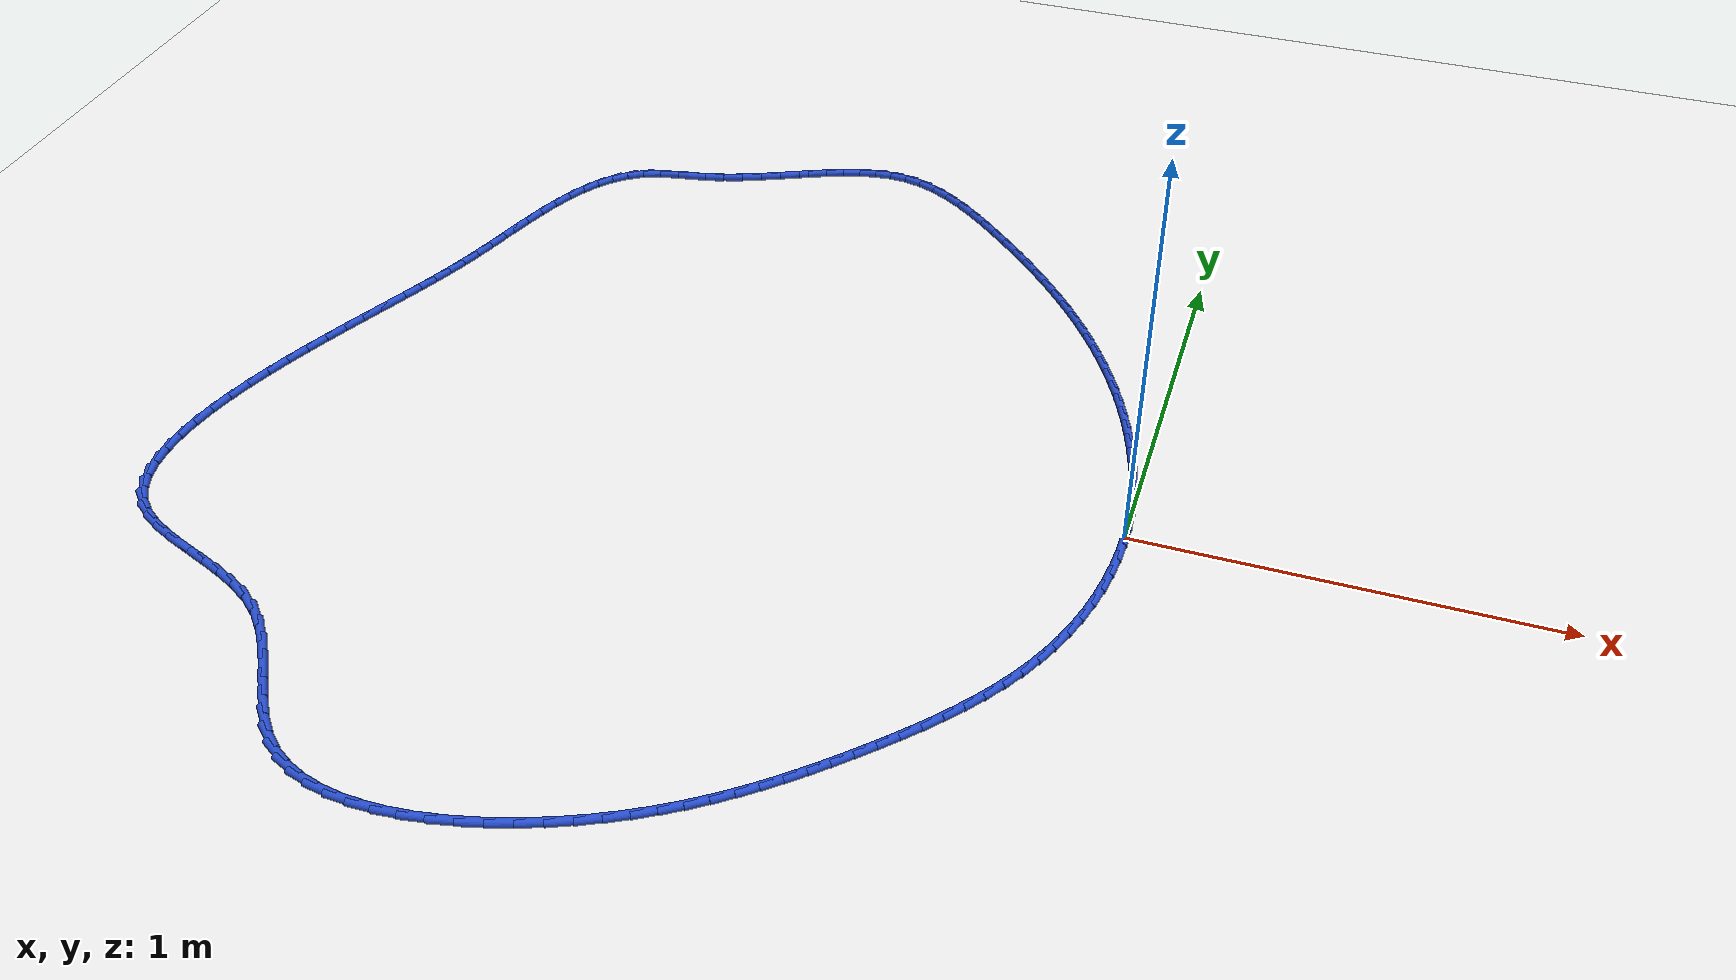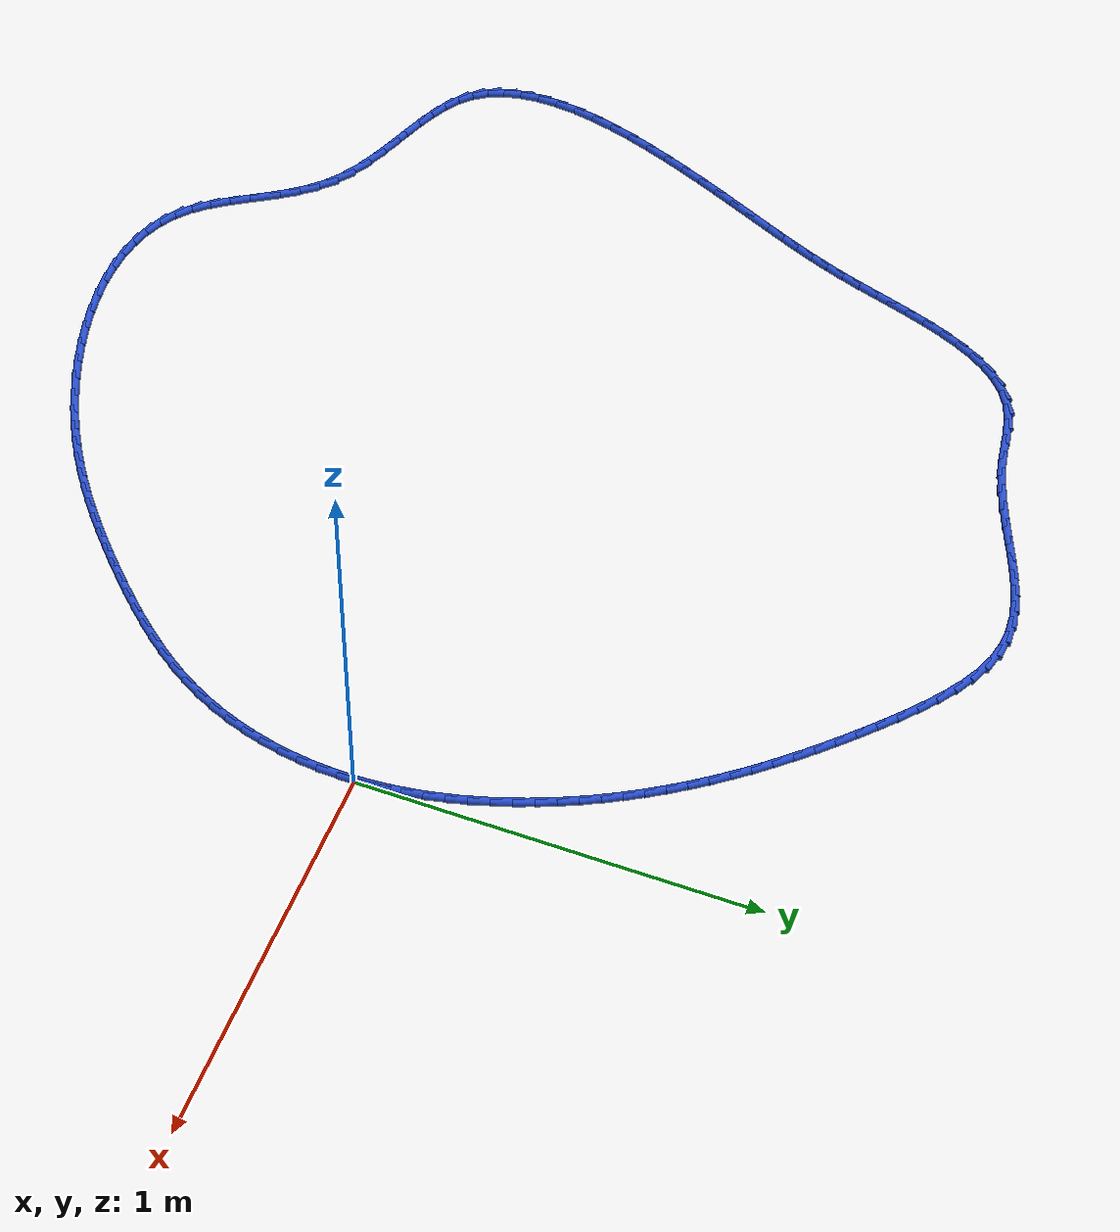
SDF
<sdf version="1.6">
 <world name="default">
  <light name="sun" type="directional">
   <pose>0 0 10 0 -0 0</pose>
   <diffuse>0.8 0.8 0.8 1</diffuse>
   <specular>0.2 0.2 0.2 1</specular>
   <attenuation>
    <range>1000</range>
    <constant>0.9</constant>
    <linear>0.01</linear>
    <quadratic>0.001</quadratic>
   </attenuation>
   <direction>-0.5 0.1 -0.9</direction>
  </light>
  <model name="ground_plane">
   <static>1</static>
   <link name="link">
    <collision name="collision">
     <geometry><plane><normal>0 0 1</normal><size>100 100</size></plane></geometry>
     <surface><friction><ode><mu>100</mu><mu2>50</mu2></ode></friction></surface>
    </collision>
    <visual name="visual">
     <cast_shadows>0</cast_shadows>
     <geometry><plane><normal>0 0 1</normal><size>100 100</size></plane></geometry>
     <material>
      <script><uri>file://media/materials/scripts/gazebo.material</uri><name>Gazebo/WhiteGlow</name></script>
     </material>
    </visual>
   </link>
  </model>
  <gravity>0 0 -9.8</gravity>
  <magnetic_field>6e-06 2.3e-05 -4.2e-05</magnetic_field>
  <atmosphere type="adiabatic"/>
  <physics name="default_physics" default="0" type="ode">
   <max_step_size>0.001</max_step_size>
   <real_time_factor>1</real_time_factor>
   <real_time_update_rate>1000</real_time_update_rate>
  </physics>
  <scene><ambient>0.4 0.4 0.4 1</ambient><background>0.7 0.7 0.7 1</background><shadows>1</shadows></scene>
  <spherical_coordinates>
   <surface_model>EARTH_WGS84</surface_model>
   <latitude_deg>0</latitude_deg>
   <longitude_deg>0</longitude_deg>
   <elevation>0</elevation>
   <heading_deg>0</heading_deg>
  </spherical_coordinates>
  <model name="line">
   <link name="link_0">
    <pose>-5.204170427930421e-17 -6.938893903907228e-17 0.01 0 1.57 -1.5257831214846944</pose>
    <collision name="collision">
     <geometry><cylinder><radius>0.01</radius><length>0.08</length></cylinder></geometry>
    </collision>
    <visual name="visual">
     <material>
      <script><name>Gazebo/Blue</name><uri>file://media/materials/scripts/gazebo.material</uri></script>
     </material>
     <geometry><cylinder><radius>0.01</radius><length>0.08</length></cylinder></geometry>
    </visual>
   </link>
   <link name="link_1">
    <pose>-0.002325660294244466 0.05163127850698241 0.01 0 1.57 -1.4733099521417214</pose>
    <collision name="collision">
     <geometry><cylinder><radius>0.01</radius><length>0.08</length></cylinder></geometry>
    </collision>
    <visual name="visual">
     <material>
      <script><name>Gazebo/Blue</name><uri>file://media/materials/scripts/gazebo.material</uri></script>
     </material>
     <geometry><cylinder><radius>0.01</radius><length>0.08</length></cylinder></geometry>
    </visual>
   </link>
   <link name="link_2">
    <pose>-0.007352197802913856 0.1030292717078458 0.01 0 1.57 -1.4235905987286477</pose>
    <collision name="collision">
     <geometry><cylinder><radius>0.01</radius><length>0.08</length></cylinder></geometry>
    </collision>
    <visual name="visual">
     <material>
      <script><name>Gazebo/Blue</name><uri>file://media/materials/scripts/gazebo.material</uri></script>
     </material>
     <geometry><cylinder><radius>0.01</radius><length>0.08</length></cylinder></geometry>
    </visual>
   </link>
   <link name="link_3">
    <pose>-0.014924133082717044 0.15409496586268012 0.01 0 1.57 -1.376536474901656</pose>
    <collision name="collision">
     <geometry><cylinder><radius>0.01</radius><length>0.08</length></cylinder></geometry>
    </collision>
    <visual name="visual">
     <material>
      <script><name>Gazebo/Blue</name><uri>file://media/materials/scripts/gazebo.material</uri></script>
     </material>
     <geometry><cylinder><radius>0.01</radius><length>0.08</length></cylinder></geometry>
    </visual>
   </link>
   <link name="link_4">
    <pose>-0.024885986690362828 0.20472934723157535 0.01 0 1.57 -1.3320208167475212</pose>
    <collision name="collision">
     <geometry><cylinder><radius>0.01</radius><length>0.08</length></cylinder></geometry>
    </collision>
    <visual name="visual">
     <material>
      <script><name>Gazebo/Blue</name><uri>file://media/materials/scripts/gazebo.material</uri></script>
     </material>
     <geometry><cylinder><radius>0.01</radius><length>0.08</length></cylinder></geometry>
    </visual>
   </link>
   <link name="link_5">
    <pose>-0.03708227918256005 0.2548334020746216 0.01 0 1.57 -1.2898895692620886</pose>
    <collision name="collision">
     <geometry><cylinder><radius>0.01</radius><length>0.08</length></cylinder></geometry>
    </collision>
    <visual name="visual">
     <material>
      <script><name>Gazebo/Blue</name><uri>file://media/materials/scripts/gazebo.material</uri></script>
     </material>
     <geometry><cylinder><radius>0.01</radius><length>0.08</length></cylinder></geometry>
    </visual>
   </link>
   <link name="link_6">
    <pose>-0.05135753111601754 0.3043081166519089 0.01 0 1.57 -1.249970216843738</pose>
    <collision name="collision">
     <geometry><cylinder><radius>0.01</radius><length>0.08</length></cylinder></geometry>
    </collision>
    <visual name="visual">
     <material>
      <script><name>Gazebo/Blue</name><uri>file://media/materials/scripts/gazebo.material</uri></script>
     </material>
     <geometry><cylinder><radius>0.01</radius><length>0.08</length></cylinder></geometry>
    </visual>
   </link>
   <link name="link_7">
    <pose>-0.06755626304744408 0.3530544772235271 0.01 0 1.57 -1.2120785289682583</pose>
    <collision name="collision">
     <geometry><cylinder><radius>0.01</radius><length>0.08</length></cylinder></geometry>
    </collision>
    <visual name="visual">
     <material>
      <script><name>Gazebo/Blue</name><uri>file://media/materials/scripts/gazebo.material</uri></script>
     </material>
     <geometry><cylinder><radius>0.01</radius><length>0.08</length></cylinder></geometry>
    </visual>
   </link>
   <link name="link_8">
    <pose>-0.0855229955335485 0.4009734700495663 0.01 0 1.57 -1.1760175319198385</pose>
    <collision name="collision">
     <geometry><cylinder><radius>0.01</radius><length>0.08</length></cylinder></geometry>
    </collision>
    <visual name="visual">
     <material>
      <script><name>Gazebo/Blue</name><uri>file://media/materials/scripts/gazebo.material</uri></script>
     </material>
     <geometry><cylinder><radius>0.01</radius><length>0.08</length></cylinder></geometry>
    </visual>
   </link>
   <link name="link_9">
    <pose>-0.1051028480615559 0.4479667474764099 0.01 0 1.57 -1.141191236776524</pose>
    <collision name="collision">
     <geometry><cylinder><radius>0.01</radius><length>0.08</length></cylinder></geometry>
    </collision>
    <visual name="visual">
     <material>
      <script><name>Gazebo/Blue</name><uri>file://media/materials/scripts/gazebo.material</uri></script>
     </material>
     <geometry><cylinder><radius>0.01</radius><length>0.08</length></cylinder></geometry>
    </visual>
   </link>
   <link name="link_10">
    <pose>-0.1261865846218613 0.49398672429633006 0.01 0 1.57 -1.1069178271526963</pose>
    <collision name="collision">
     <geometry><cylinder><radius>0.01</radius><length>0.08</length></cylinder></geometry>
    </collision>
    <visual name="visual">
     <material>
      <script><name>Gazebo/Blue</name><uri>file://media/materials/scripts/gazebo.material</uri></script>
     </material>
     <geometry><cylinder><radius>0.01</radius><length>0.08</length></cylinder></geometry>
    </visual>
   </link>
   <link name="link_11">
    <pose>-0.14874194966209112 0.5390714272816475 0.01 0 1.57 -1.0732754120545926</pose>
    <collision name="collision">
     <geometry><cylinder><radius>0.01</radius><length>0.08</length></cylinder></geometry>
    </collision>
    <visual name="visual">
     <material>
      <script><name>Gazebo/Blue</name><uri>file://media/materials/scripts/gazebo.material</uri></script>
     </material>
     <geometry><cylinder><radius>0.01</radius><length>0.08</length></cylinder></geometry>
    </visual>
   </link>
   <link name="link_12">
    <pose>-0.17274409558982812 0.5832671217907192 0.01 0 1.57 -1.0404040914403896</pose>
    <collision name="collision">
     <geometry><cylinder><radius>0.01</radius><length>0.08</length></cylinder></geometry>
    </collision>
    <visual name="visual">
     <material>
      <script><name>Gazebo/Blue</name><uri>file://media/materials/scripts/gazebo.material</uri></script>
     </material>
     <geometry><cylinder><radius>0.01</radius><length>0.08</length></cylinder></geometry>
    </visual>
   </link>
   <link name="link_13">
    <pose>-0.19816817481265495 0.6266200731819013 0.01 0 1.57 -1.0084315196574196</pose>
    <collision name="collision">
     <geometry><cylinder><radius>0.01</radius><length>0.08</length></cylinder></geometry>
    </collision>
    <visual name="visual">
     <material>
      <script><name>Gazebo/Blue</name><uri>file://media/materials/scripts/gazebo.material</uri></script>
     </material>
     <geometry><cylinder><radius>0.01</radius><length>0.08</length></cylinder></geometry>
    </visual>
   </link>
   <link name="link_14">
    <pose>-0.22498933973815452 0.6691765468135512 0.01 0 1.57 -0.9774711283294925</pose>
    <collision name="collision">
     <geometry><cylinder><radius>0.01</radius><length>0.08</length></cylinder></geometry>
    </collision>
    <visual name="visual">
     <material>
      <script><name>Gazebo/Blue</name><uri>file://media/materials/scripts/gazebo.material</uri></script>
     </material>
     <geometry><cylinder><radius>0.01</radius><length>0.08</length></cylinder></geometry>
    </visual>
   </link>
   <link name="link_15">
    <pose>-0.2531827427739095 0.7109828080440254 0.01 0 1.57 -0.9476209765600271</pose>
    <collision name="collision">
     <geometry><cylinder><radius>0.01</radius><length>0.08</length></cylinder></geometry>
    </collision>
    <visual name="visual">
     <material>
      <script><name>Gazebo/Blue</name><uri>file://media/materials/scripts/gazebo.material</uri></script>
     </material>
     <geometry><cylinder><radius>0.01</radius><length>0.08</length></cylinder></geometry>
    </visual>
   </link>
   <link name="link_16">
    <pose>-0.2827235363275028 0.7520851222316806 0.01 0 1.57 -0.9189632152893463</pose>
    <collision name="collision">
     <geometry><cylinder><radius>0.01</radius><length>0.08</length></cylinder></geometry>
    </collision>
    <visual name="visual">
     <material>
      <script><name>Gazebo/Blue</name><uri>file://media/materials/scripts/gazebo.material</uri></script>
     </material>
     <geometry><cylinder><radius>0.01</radius><length>0.08</length></cylinder></geometry>
    </visual>
   </link>
   <link name="link_17">
    <pose>-0.3135868728065171 0.7925297547348739 0.01 0 1.57 -0.8915641136599226</pose>
    <collision name="collision">
     <geometry><cylinder><radius>0.01</radius><length>0.08</length></cylinder></geometry>
    </collision>
    <visual name="visual">
     <material>
      <script><name>Gazebo/Blue</name><uri>file://media/materials/scripts/gazebo.material</uri></script>
     </material>
     <geometry><cylinder><radius>0.01</radius><length>0.08</length></cylinder></geometry>
    </visual>
   </link>
   <link name="link_18">
    <pose>-0.345747904618535 0.8323629709119614 0.01 0 1.57 -0.8654745670512032</pose>
    <collision name="collision">
     <geometry><cylinder><radius>0.01</radius><length>0.08</length></cylinder></geometry>
    </collision>
    <visual name="visual">
     <material>
      <script><name>Gazebo/Blue</name><uri>file://media/materials/scripts/gazebo.material</uri></script>
     </material>
     <geometry><cylinder><radius>0.01</radius><length>0.08</length></cylinder></geometry>
    </visual>
   </link>
   <link name="link_19">
    <pose>-0.3791817841711396 0.8716310361213007 0.01 0 1.57 -0.8407309900000115</pose>
    <collision name="collision">
     <geometry><cylinder><radius>0.01</radius><length>0.08</length></cylinder></geometry>
    </collision>
    <visual name="visual">
     <material>
      <script><name>Gazebo/Blue</name><uri>file://media/materials/scripts/gazebo.material</uri></script>
     </material>
     <geometry><cylinder><radius>0.01</radius><length>0.08</length></cylinder></geometry>
    </visual>
   </link>
   <link name="link_20">
    <pose>-0.4138636638719136 0.9103802157212478 0.01 0 1.57 -0.8173564917610722</pose>
    <collision name="collision">
     <geometry><cylinder><radius>0.01</radius><length>0.08</length></cylinder></geometry>
    </collision>
    <visual name="visual">
     <material>
      <script><name>Gazebo/Blue</name><uri>file://media/materials/scripts/gazebo.material</uri></script>
     </material>
     <geometry><cylinder><radius>0.01</radius><length>0.08</length></cylinder></geometry>
    </visual>
   </link>
   <link name="link_21">
    <pose>-0.4497686961284397 0.9486567750701602 0.01 0 1.57 -0.7953622358415272</pose>
    <collision name="collision">
     <geometry><cylinder><radius>0.01</radius><length>0.08</length></cylinder></geometry>
    </collision>
    <visual name="visual">
     <material>
      <script><name>Gazebo/Blue</name><uri>file://media/materials/scripts/gazebo.material</uri></script>
     </material>
     <geometry><cylinder><radius>0.01</radius><length>0.08</length></cylinder></geometry>
    </visual>
   </link>
   <link name="link_22">
    <pose>-0.48687203334830065 0.9865069795263941 0.01 0 1.57 -0.7747488949391926</pose>
    <collision name="collision">
     <geometry><cylinder><radius>0.01</radius><length>0.08</length></cylinder></geometry>
    </collision>
    <visual name="visual">
     <material>
      <script><name>Gazebo/Blue</name><uri>file://media/materials/scripts/gazebo.material</uri></script>
     </material>
     <geometry><cylinder><radius>0.01</radius><length>0.08</length></cylinder></geometry>
    </visual>
   </link>
   <link name="link_23">
    <pose>-0.5251488279390792 1.0239770944483064 0.01 0 1.57 -0.7555081267369648</pose>
    <collision name="collision">
     <geometry><cylinder><radius>0.01</radius><length>0.08</length></cylinder></geometry>
    </collision>
    <visual name="visual">
     <material>
      <script><name>Gazebo/Blue</name><uri>file://media/materials/scripts/gazebo.material</uri></script>
     </material>
     <geometry><cylinder><radius>0.01</radius><length>0.08</length></cylinder></geometry>
    </visual>
   </link>
   <link name="link_24">
    <pose>-0.5645742323083585 1.061113385194254 0.01 0 1.57 -0.7375607450228647</pose>
    <collision name="collision">
     <geometry><cylinder><radius>0.01</radius><length>0.08</length></cylinder></geometry>
    </collision>
    <visual name="visual">
     <material>
      <script><name>Gazebo/Blue</name><uri>file://media/materials/scripts/gazebo.material</uri></script>
     </material>
     <geometry><cylinder><radius>0.01</radius><length>0.08</length></cylinder></geometry>
    </visual>
   </link>
   <link name="link_25">
    <pose>-0.6051230668936379 1.0979571317987191 0.01 0 1.57 -0.7158475545662858</pose>
    <collision name="collision">
     <geometry><cylinder><radius>0.01</radius><length>0.08</length></cylinder></geometry>
    </collision>
    <visual name="visual">
     <material>
      <script><name>Gazebo/Blue</name><uri>file://media/materials/scripts/gazebo.material</uri></script>
     </material>
     <geometry><cylinder><radius>0.01</radius><length>0.08</length></cylinder></geometry>
    </visual>
   </link>
   <link name="link_26">
    <pose>-0.6467439978595596 1.1341568454062452 0.01 0 1.57 -0.6812446581881678</pose>
    <collision name="collision">
     <geometry><cylinder><radius>0.01</radius><length>0.08</length></cylinder></geometry>
    </collision>
    <visual name="visual">
     <material>
      <script><name>Gazebo/Blue</name><uri>file://media/materials/scripts/gazebo.material</uri></script>
     </material>
     <geometry><cylinder><radius>0.01</radius><length>0.08</length></cylinder></geometry>
    </visual>
   </link>
   <link name="link_27">
    <pose>-0.6893410903849608 1.1686912468070636 0.01 0 1.57 -0.6312850540638846</pose>
    <collision name="collision">
     <geometry><cylinder><radius>0.01</radius><length>0.08</length></cylinder></geometry>
    </collision>
    <visual name="visual">
     <material>
      <script><name>Gazebo/Blue</name><uri>file://media/materials/scripts/gazebo.material</uri></script>
     </material>
     <geometry><cylinder><radius>0.01</radius><length>0.08</length></cylinder></geometry>
    </visual>
   </link>
   <link name="link_28">
    <pose>-0.7328140555634766 1.2004736698001028 0.01 0 1.57 -0.5632730678353299</pose>
    <collision name="collision">
     <geometry><cylinder><radius>0.01</radius><length>0.08</length></cylinder></geometry>
    </collision>
    <visual name="visual">
     <material>
      <script><name>Gazebo/Blue</name><uri>file://media/materials/scripts/gazebo.material</uri></script>
     </material>
     <geometry><cylinder><radius>0.01</radius><length>0.08</length></cylinder></geometry>
    </visual>
   </link>
   <link name="link_29">
    <pose>-0.7770626044887409 1.2284174481842904 0.01 0 1.57 -0.4735093367927322</pose>
    <collision name="collision">
     <geometry><cylinder><radius>0.01</radius><length>0.08</length></cylinder></geometry>
    </collision>
    <visual name="visual">
     <material>
      <script><name>Gazebo/Blue</name><uri>file://media/materials/scripts/gazebo.material</uri></script>
     </material>
     <geometry><cylinder><radius>0.01</radius><length>0.08</length></cylinder></geometry>
    </visual>
   </link>
   <link name="link_30">
    <pose>-0.8219864482543884 1.2514359157585553 0.01 0 1.57 -0.35769931263048116</pose>
    <collision name="collision">
     <geometry><cylinder><radius>0.01</radius><length>0.08</length></cylinder></geometry>
    </collision>
    <visual name="visual">
     <material>
      <script><name>Gazebo/Blue</name><uri>file://media/materials/scripts/gazebo.material</uri></script>
     </material>
     <geometry><cylinder><radius>0.01</radius><length>0.08</length></cylinder></geometry>
    </visual>
   </link>
   <link name="link_31">
    <pose>-0.8674852979540536 1.2684424063218258 0.01 0 1.57 -0.21226533550293</pose>
    <collision name="collision">
     <geometry><cylinder><radius>0.01</radius><length>0.08</length></cylinder></geometry>
    </collision>
    <visual name="visual">
     <material>
      <script><name>Gazebo/Blue</name><uri>file://media/materials/scripts/gazebo.material</uri></script>
     </material>
     <geometry><cylinder><radius>0.01</radius><length>0.08</length></cylinder></geometry>
    </visual>
   </link>
   <link name="link_32">
    <pose>-0.9134588647213701 1.2783502543558156 0.01 0 1.57 -0.045566969543972664</pose>
    <collision name="collision">
     <geometry><cylinder><radius>0.01</radius><length>0.08</length></cylinder></geometry>
    </collision>
    <visual name="visual">
     <material>
      <script><name>Gazebo/Blue</name><uri>file://media/materials/scripts/gazebo.material</uri></script>
     </material>
     <geometry><cylinder><radius>0.01</radius><length>0.08</length></cylinder></geometry>
    </visual>
   </link>
   <link name="link_33">
    <pose>-0.9598298185924168 1.2804647018446382 0.01 0 1.57 0.10356913467731238</pose>
    <collision name="collision">
     <geometry><cylinder><radius>0.01</radius><length>0.08</length></cylinder></geometry>
    </collision>
    <visual name="visual">
     <material>
      <script><name>Gazebo/Blue</name><uri>file://media/materials/scripts/gazebo.material</uri></script>
     </material>
     <geometry><cylinder><radius>0.01</radius><length>0.08</length></cylinder></geometry>
    </visual>
   </link>
   <link name="link_34">
    <pose>-1.0066093708612658 1.275602386335011 0.01 0 1.57 0.22198942262711954</pose>
    <collision name="collision">
     <geometry><cylinder><radius>0.01</radius><length>0.08</length></cylinder></geometry>
    </collision>
    <visual name="visual">
     <material>
      <script><name>Gazebo/Blue</name><uri>file://media/materials/scripts/gazebo.material</uri></script>
     </material>
     <geometry><cylinder><radius>0.01</radius><length>0.08</length></cylinder></geometry>
    </visual>
   </link>
   <link name="link_35">
    <pose>-1.0538300738862896 1.264944236446754 0.01 0 1.57 0.30990920765176827</pose>
    <collision name="collision">
     <geometry><cylinder><radius>0.01</radius><length>0.08</length></cylinder></geometry>
    </collision>
    <visual name="visual">
     <material>
      <script><name>Gazebo/Blue</name><uri>file://media/materials/scripts/gazebo.material</uri></script>
     </material>
     <geometry><cylinder><radius>0.01</radius><length>0.08</length></cylinder></geometry>
    </visual>
   </link>
   <link name="link_36">
    <pose>-1.1015244800258608 1.2496711807996874 0.01 0 1.57 0.3702122707655162</pose>
    <collision name="collision">
     <geometry><cylinder><radius>0.01</radius><length>0.08</length></cylinder></geometry>
    </collision>
    <visual name="visual">
     <material>
      <script><name>Gazebo/Blue</name><uri>file://media/materials/scripts/gazebo.material</uri></script>
     </material>
     <geometry><cylinder><radius>0.01</radius><length>0.08</length></cylinder></geometry>
    </visual>
   </link>
   <link name="link_37">
    <pose>-1.1497251416383534 1.2309641480136317 0.01 0 1.57 0.40613458403579866</pose>
    <collision name="collision">
     <geometry><cylinder><radius>0.01</radius><length>0.08</length></cylinder></geometry>
    </collision>
    <visual name="visual">
     <material>
      <script><name>Gazebo/Blue</name><uri>file://media/materials/scripts/gazebo.material</uri></script>
     </material>
     <geometry><cylinder><radius>0.01</radius><length>0.08</length></cylinder></geometry>
    </visual>
   </link>
   <link name="link_38">
    <pose>-1.1984646110821398 1.2100040667084075 0.01 0 1.57 0.4201916904959871</pose>
    <collision name="collision">
     <geometry><cylinder><radius>0.01</radius><length>0.08</length></cylinder></geometry>
    </collision>
    <visual name="visual">
     <material>
      <script><name>Gazebo/Blue</name><uri>file://media/materials/scripts/gazebo.material</uri></script>
     </material>
     <geometry><cylinder><radius>0.01</radius><length>0.08</length></cylinder></geometry>
    </visual>
   </link>
   <link name="link_39">
    <pose>-1.2477754407155939 1.187971865503835 0.01 0 1.57 0.413850504690845</pose>
    <collision name="collision">
     <geometry><cylinder><radius>0.01</radius><length>0.08</length></cylinder></geometry>
    </collision>
    <visual name="visual">
     <material>
      <script><name>Gazebo/Blue</name><uri>file://media/materials/scripts/gazebo.material</uri></script>
     </material>
     <geometry><cylinder><radius>0.01</radius><length>0.08</length></cylinder></geometry>
    </visual>
   </link>
   <link name="link_40">
    <pose>-1.2976901828970884 1.1660484730197351 0.01 0 1.57 0.3875324435079767</pose>
    <collision name="collision">
     <geometry><cylinder><radius>0.01</radius><length>0.08</length></cylinder></geometry>
    </collision>
    <visual name="visual">
     <material>
      <script><name>Gazebo/Blue</name><uri>file://media/materials/scripts/gazebo.material</uri></script>
     </material>
     <geometry><cylinder><radius>0.01</radius><length>0.08</length></cylinder></geometry>
    </visual>
   </link>
   <link name="link_41">
    <pose>-1.3482413899849963 1.1454148178759276 0.01 0 1.57 0.34077208446727003</pose>
    <collision name="collision">
     <geometry><cylinder><radius>0.01</radius><length>0.08</length></cylinder></geometry>
    </collision>
    <visual name="visual">
     <material>
      <script><name>Gazebo/Blue</name><uri>file://media/materials/scripts/gazebo.material</uri></script>
     </material>
     <geometry><cylinder><radius>0.01</radius><length>0.08</length></cylinder></geometry>
    </visual>
   </link>
   <link name="link_42">
    <pose>-1.3994616143376908 1.1272518286922328 0.01 0 1.57 0.2725316518254183</pose>
    <collision name="collision">
     <geometry><cylinder><radius>0.01</radius><length>0.08</length></cylinder></geometry>
    </collision>
    <visual name="visual">
     <material>
      <script><name>Gazebo/Blue</name><uri>file://media/materials/scripts/gazebo.material</uri></script>
     </material>
     <geometry><cylinder><radius>0.01</radius><length>0.08</length></cylinder></geometry>
    </visual>
   </link>
   <link name="link_43">
    <pose>-1.4513834083135457 1.112740434088472 0.01 0 1.57 0.19591030809090093</pose>
    <collision name="collision">
     <geometry><cylinder><radius>0.01</radius><length>0.08</length></cylinder></geometry>
    </collision>
    <visual name="visual">
     <material>
      <script><name>Gazebo/Blue</name><uri>file://media/materials/scripts/gazebo.material</uri></script>
     </material>
     <geometry><cylinder><radius>0.01</radius><length>0.08</length></cylinder></geometry>
    </visual>
   </link>
   <link name="link_44">
    <pose>-1.5037814707765587 1.1023417349070572 0.01 0 1.57 0.17346217587245516</pose>
    <collision name="collision">
     <geometry><cylinder><radius>0.01</radius><length>0.08</length></cylinder></geometry>
    </collision>
    <visual name="visual">
     <material>
      <script><name>Gazebo/Blue</name><uri>file://media/materials/scripts/gazebo.material</uri></script>
     </material>
     <geometry><cylinder><radius>0.01</radius><length>0.08</length></cylinder></geometry>
    </visual>
   </link>
   <link name="link_45">
    <pose>-1.5552843560217884 1.093317237198611 0.01 0 1.57 0.22657988994246744</pose>
    <collision name="collision">
     <geometry><cylinder><radius>0.01</radius><length>0.08</length></cylinder></geometry>
    </collision>
    <visual name="visual">
     <material>
      <script><name>Gazebo/Blue</name><uri>file://media/materials/scripts/gazebo.material</uri></script>
     </material>
     <geometry><cylinder><radius>0.01</radius><length>0.08</length></cylinder></geometry>
    </visual>
   </link>
   <link name="link_46">
    <pose>-1.6042022791810313 1.0820397665135777 0.01 0 1.57 0.36633878095691547</pose>
    <collision name="collision">
     <geometry><cylinder><radius>0.01</radius><length>0.08</length></cylinder></geometry>
    </collision>
    <visual name="visual">
     <material>
      <script><name>Gazebo/Blue</name><uri>file://media/materials/scripts/gazebo.material</uri></script>
     </material>
     <geometry><cylinder><radius>0.01</radius><length>0.08</length></cylinder></geometry>
    </visual>
   </link>
   <link name="link_47">
    <pose>-1.6488576826133392 1.0649074034522743 0.01 0 1.57 0.5626558504823563</pose>
    <collision name="collision">
     <geometry><cylinder><radius>0.01</radius><length>0.08</length></cylinder></geometry>
    </collision>
    <visual name="visual">
     <material>
      <script><name>Gazebo/Blue</name><uri>file://media/materials/scripts/gazebo.material</uri></script>
     </material>
     <geometry><cylinder><radius>0.01</radius><length>0.08</length></cylinder></geometry>
    </visual>
   </link>
   <link name="link_48">
    <pose>-1.6883788100728876 1.0399831874981553 0.01 0 1.57 0.7431528773780378</pose>
    <collision name="collision">
     <geometry><cylinder><radius>0.01</radius><length>0.08</length></cylinder></geometry>
    </collision>
    <visual name="visual">
     <material>
      <script><name>Gazebo/Blue</name><uri>file://media/materials/scripts/gazebo.material</uri></script>
     </material>
     <geometry><cylinder><radius>0.01</radius><length>0.08</length></cylinder></geometry>
    </visual>
   </link>
   <link name="link_49">
    <pose>-1.7231857931687031 1.0079994761241602 0.01 0 1.57 0.8932933806143348</pose>
    <collision name="collision">
     <geometry><cylinder><radius>0.01</radius><length>0.08</length></cylinder></geometry>
    </collision>
    <visual name="visual">
     <material>
      <script><name>Gazebo/Blue</name><uri>file://media/materials/scripts/gazebo.material</uri></script>
     </material>
     <geometry><cylinder><radius>0.01</radius><length>0.08</length></cylinder></geometry>
    </visual>
   </link>
   <link name="link_50">
    <pose>-1.753815062928314 0.9699289263995137 0.01 0 1.57 1.0122381327909464</pose>
    <collision name="collision">
     <geometry><cylinder><radius>0.01</radius><length>0.08</length></cylinder></geometry>
    </collision>
    <visual name="visual">
     <material>
      <script><name>Gazebo/Blue</name><uri>file://media/materials/scripts/gazebo.material</uri></script>
     </material>
     <geometry><cylinder><radius>0.01</radius><length>0.08</length></cylinder></geometry>
    </visual>
   </link>
   <link name="link_51">
    <pose>-1.7808030503792458 0.9267441953934396 0.01 0 1.57 1.1034366268510836</pose>
    <collision name="collision">
     <geometry><cylinder><radius>0.01</radius><length>0.08</length></cylinder></geometry>
    </collision>
    <visual name="visual">
     <material>
      <script><name>Gazebo/Blue</name><uri>file://media/materials/scripts/gazebo.material</uri></script>
     </material>
     <geometry><cylinder><radius>0.01</radius><length>0.08</length></cylinder></geometry>
    </visual>
   </link>
   <link name="link_52">
    <pose>-1.8046861865490258 0.8794179401751617 0.01 0 1.57 1.1713723848398787</pose>
    <collision name="collision">
     <geometry><cylinder><radius>0.01</radius><length>0.08</length></cylinder></geometry>
    </collision>
    <visual name="visual">
     <material>
      <script><name>Gazebo/Blue</name><uri>file://media/materials/scripts/gazebo.material</uri></script>
     </material>
     <geometry><cylinder><radius>0.01</radius><length>0.08</length></cylinder></geometry>
    </visual>
   </link>
   <link name="link_53">
    <pose>-1.8260009024651807 0.8289228178139051 0.01 0 1.57 1.2199778294461034</pose>
    <collision name="collision">
     <geometry><cylinder><radius>0.01</radius><length>0.08</length></cylinder></geometry>
    </collision>
    <visual name="visual">
     <material>
      <script><name>Gazebo/Blue</name><uri>file://media/materials/scripts/gazebo.material</uri></script>
     </material>
     <geometry><cylinder><radius>0.01</radius><length>0.08</length></cylinder></geometry>
    </visual>
   </link>
   <link name="link_54">
    <pose>-1.8452836291552381 0.7762314853788934 0.01 0 1.57 1.2521281128866246</pose>
    <collision name="collision">
     <geometry><cylinder><radius>0.01</radius><length>0.08</length></cylinder></geometry>
    </collision>
    <visual name="visual">
     <material>
      <script><name>Gazebo/Blue</name><uri>file://media/materials/scripts/gazebo.material</uri></script>
     </material>
     <geometry><cylinder><radius>0.01</radius><length>0.08</length></cylinder></geometry>
    </visual>
   </link>
   <link name="link_55">
    <pose>-1.8630707976467238 0.7223165999393505 0.01 0 1.57 1.2695734866179076</pose>
    <collision name="collision">
     <geometry><cylinder><radius>0.01</radius><length>0.08</length></cylinder></geometry>
    </collision>
    <visual name="visual">
     <material>
      <script><name>Gazebo/Blue</name><uri>file://media/materials/scripts/gazebo.material</uri></script>
     </material>
     <geometry><cylinder><radius>0.01</radius><length>0.08</length></cylinder></geometry>
    </visual>
   </link>
   <link name="link_56">
    <pose>-1.879898838967165 0.6681508185645015 0.01 0 1.57 1.2729636206471848</pose>
    <collision name="collision">
     <geometry><cylinder><radius>0.01</radius><length>0.08</length></cylinder></geometry>
    </collision>
    <visual name="visual">
     <material>
      <script><name>Gazebo/Blue</name><uri>file://media/materials/scripts/gazebo.material</uri></script>
     </material>
     <geometry><cylinder><radius>0.01</radius><length>0.08</length></cylinder></geometry>
    </visual>
   </link>
   <link name="link_57">
    <pose>-1.8963041841440882 0.6147067983235692 0.01 0 1.57 1.26180859358023</pose>
    <collision name="collision">
     <geometry><cylinder><radius>0.01</radius><length>0.08</length></cylinder></geometry>
    </collision>
    <visual name="visual">
     <material>
      <script><name>Gazebo/Blue</name><uri>file://media/materials/scripts/gazebo.material</uri></script>
     </material>
     <geometry><cylinder><radius>0.01</radius><length>0.08</length></cylinder></geometry>
    </visual>
   </link>
   <link name="link_58">
    <pose>-1.9128232642050205 0.5629571962857793 0.01 0 1.57 1.2374722600116919</pose>
    <collision name="collision">
     <geometry><cylinder><radius>0.01</radius><length>0.08</length></cylinder></geometry>
    </collision>
    <visual name="visual">
     <material>
      <script><name>Gazebo/Blue</name><uri>file://media/materials/scripts/gazebo.material</uri></script>
     </material>
     <geometry><cylinder><radius>0.01</radius><length>0.08</length></cylinder></geometry>
    </visual>
   </link>
   <link name="link_59">
    <pose>-1.9299136742801908 0.5135976378696189 0.01 0 1.57 1.2117654814617043</pose>
    <collision name="collision">
     <geometry><cylinder><radius>0.01</radius><length>0.08</length></cylinder></geometry>
    </collision>
    <visual name="visual">
     <material>
      <script><name>Gazebo/Blue</name><uri>file://media/materials/scripts/gazebo.material</uri></script>
     </material>
     <geometry><cylinder><radius>0.01</radius><length>0.08</length></cylinder></geometry>
    </visual>
   </link>
   <link name="link_60">
    <pose>-1.9477083192489788 0.46618277744797815 0.01 0 1.57 1.189086762597426</pose>
    <collision name="collision">
     <geometry><cylinder><radius>0.01</radius><length>0.08</length></cylinder></geometry>
    </collision>
    <visual name="visual">
     <material>
      <script><name>Gazebo/Blue</name><uri>file://media/materials/scripts/gazebo.material</uri></script>
     </material>
     <geometry><cylinder><radius>0.01</radius><length>0.08</length></cylinder></geometry>
    </visual>
   </link>
   <link name="link_61">
    <pose>-1.9662565259195908 0.4199735736051998 0.01 0 1.57 1.170584200995082</pose>
    <collision name="collision">
     <geometry><cylinder><radius>0.01</radius><length>0.08</length></cylinder></geometry>
    </collision>
    <visual name="visual">
     <material>
      <script><name>Gazebo/Blue</name><uri>file://media/materials/scripts/gazebo.material</uri></script>
     </material>
     <geometry><cylinder><radius>0.01</radius><length>0.08</length></cylinder></geometry>
    </visual>
   </link>
   <link name="link_62">
    <pose>-1.9856076210253153 0.3742309846623678 0.01 0 1.57 1.1570780334080306</pose>
    <collision name="collision">
     <geometry><cylinder><radius>0.01</radius><length>0.08</length></cylinder></geometry>
    </collision>
    <visual name="visual">
     <material>
      <script><name>Gazebo/Blue</name><uri>file://media/materials/scripts/gazebo.material</uri></script>
     </material>
     <geometry><cylinder><radius>0.01</radius><length>0.08</length></cylinder></geometry>
    </visual>
   </link>
   <link name="link_63">
    <pose>-2.0058109312994414 0.32821596894056543 0.01 0 1.57 1.148951989883893</pose>
    <collision name="collision">
     <geometry><cylinder><radius>0.01</radius><length>0.08</length></cylinder></geometry>
    </collision>
    <visual name="visual">
     <material>
      <script><name>Gazebo/Blue</name><uri>file://media/materials/scripts/gazebo.material</uri></script>
     </material>
     <geometry><cylinder><radius>0.01</radius><length>0.08</length></cylinder></geometry>
    </visual>
   </link>
   <link name="link_64">
    <pose>-2.02691578347526 0.28118948476087713 0.01 0 1.57 1.1461354242587467</pose>
    <collision name="collision">
     <geometry><cylinder><radius>0.01</radius><length>0.08</length></cylinder></geometry>
    </collision>
    <visual name="visual">
     <material>
      <script><name>Gazebo/Blue</name><uri>file://media/materials/scripts/gazebo.material</uri></script>
     </material>
     <geometry><cylinder><radius>0.01</radius><length>0.08</length></cylinder></geometry>
    </visual>
   </link>
   <link name="link_65">
    <pose>-2.048971504286057 0.232412490444386 0.01 0 1.57 1.1482186597870714</pose>
    <collision name="collision">
     <geometry><cylinder><radius>0.01</radius><length>0.08</length></cylinder></geometry>
    </collision>
    <visual name="visual">
     <material>
      <script><name>Gazebo/Blue</name><uri>file://media/materials/scripts/gazebo.material</uri></script>
     </material>
     <geometry><cylinder><radius>0.01</radius><length>0.08</length></cylinder></geometry>
    </visual>
   </link>
   <link name="link_66">
    <pose>-2.071974319836792 0.1812573632136611 0.01 0 1.57 1.1549253689024073</pose>
    <collision name="collision">
     <geometry><cylinder><radius>0.01</radius><length>0.08</length></cylinder></geometry>
    </collision>
    <visual name="visual">
     <material>
      <script><name>Gazebo/Blue</name><uri>file://media/materials/scripts/gazebo.material</uri></script>
     </material>
     <geometry><cylinder><radius>0.01</radius><length>0.08</length></cylinder></geometry>
    </visual>
   </link>
   <link name="link_67">
    <pose>-2.0955508211085165 0.12787207072681298 0.01 0 1.57 1.16607057548934</pose>
    <collision name="collision">
     <geometry><cylinder><radius>0.01</radius><length>0.08</length></cylinder></geometry>
    </collision>
    <visual name="visual">
     <material>
      <script><name>Gazebo/Blue</name><uri>file://media/materials/scripts/gazebo.material</uri></script>
     </material>
     <geometry><cylinder><radius>0.01</radius><length>0.08</length></cylinder></geometry>
    </visual>
   </link>
   <link name="link_68">
    <pose>-2.119170450982917 0.07273431814510166 0.01 0 1.57 1.18165367795067</pose>
    <collision name="collision">
     <geometry><cylinder><radius>0.01</radius><length>0.08</length></cylinder></geometry>
    </collision>
    <visual name="visual">
     <material>
      <script><name>Gazebo/Blue</name><uri>file://media/materials/scripts/gazebo.material</uri></script>
     </material>
     <geometry><cylinder><radius>0.01</radius><length>0.08</length></cylinder></geometry>
    </visual>
   </link>
   <link name="link_69">
    <pose>-2.142302076447644 0.016323019004954198 0.01 0 1.57 1.2019453493848802</pose>
    <collision name="collision">
     <geometry><cylinder><radius>0.01</radius><length>0.08</length></cylinder></geometry>
    </collision>
    <visual name="visual">
     <material>
      <script><name>Gazebo/Blue</name><uri>file://media/materials/scripts/gazebo.material</uri></script>
     </material>
     <geometry><cylinder><radius>0.01</radius><length>0.08</length></cylinder></geometry>
    </visual>
   </link>
   <link name="link_70">
    <pose>-2.1644145644903503 -0.04088291315720414 0.01 0 1.57 1.227483008378057</pose>
    <collision name="collision">
     <geometry><cylinder><radius>0.01</radius><length>0.08</length></cylinder></geometry>
    </collision>
    <visual name="visual">
     <material>
      <script><name>Gazebo/Blue</name><uri>file://media/materials/scripts/gazebo.material</uri></script>
     </material>
     <geometry><cylinder><radius>0.01</radius><length>0.08</length></cylinder></geometry>
    </visual>
   </link>
   <link name="link_71">
    <pose>-2.1849767820986874 -0.09840456480494618 0.01 0 1.57 1.2591002900541675</pose>
    <collision name="collision">
     <geometry><cylinder><radius>0.01</radius><length>0.08</length></cylinder></geometry>
    </collision>
    <visual name="visual">
     <material>
      <script><name>Gazebo/Blue</name><uri>file://media/materials/scripts/gazebo.material</uri></script>
     </material>
     <geometry><cylinder><radius>0.01</radius><length>0.08</length></cylinder></geometry>
    </visual>
   </link>
   <link name="link_72">
    <pose>-2.2034575962603085 -0.15576302240184642 0.01 0 1.57 1.2979887422009302</pose>
    <collision name="collision">
     <geometry><cylinder><radius>0.01</radius><length>0.08</length></cylinder></geometry>
    </collision>
    <visual name="visual">
     <material>
      <script><name>Gazebo/Blue</name><uri>file://media/materials/scripts/gazebo.material</uri></script>
     </material>
     <geometry><cylinder><radius>0.01</radius><length>0.08</length></cylinder></geometry>
    </visual>
   </link>
   <link name="link_73">
    <pose>-2.2193258739628656 -0.21247937241147932 0.01 0 1.57 1.345792793061231</pose>
    <collision name="collision">
     <geometry><cylinder><radius>0.01</radius><length>0.08</length></cylinder></geometry>
    </collision>
    <visual name="visual">
     <material>
      <script><name>Gazebo/Blue</name><uri>file://media/materials/scripts/gazebo.material</uri></script>
     </material>
     <geometry><cylinder><radius>0.01</radius><length>0.08</length></cylinder></geometry>
    </visual>
   </link>
   <link name="link_74">
    <pose>-2.2320504821940093 -0.2680747012974172 0.01 0 1.57 1.4047364782906486</pose>
    <collision name="collision">
     <geometry><cylinder><radius>0.01</radius><length>0.08</length></cylinder></geometry>
    </collision>
    <visual name="visual">
     <material>
      <script><name>Gazebo/Blue</name><uri>file://media/materials/scripts/gazebo.material</uri></script>
     </material>
     <geometry><cylinder><radius>0.01</radius><length>0.08</length></cylinder></geometry>
    </visual>
   </link>
   <link name="link_75">
    <pose>-2.2411002879413933 -0.3220700955232346 0.01 0 1.57 1.4777645646208695</pose>
    <collision name="collision">
     <geometry><cylinder><radius>0.01</radius><length>0.08</length></cylinder></geometry>
    </collision>
    <visual name="visual">
     <material>
      <script><name>Gazebo/Blue</name><uri>file://media/materials/scripts/gazebo.material</uri></script>
     </material>
     <geometry><cylinder><radius>0.01</radius><length>0.08</length></cylinder></geometry>
    </visual>
   </link>
   <link name="link_76">
    <pose>-2.24594415819267 -0.3739866415525056 0.01 0 1.57 1.5686325462710848</pose>
    <collision name="collision">
     <geometry><cylinder><radius>0.01</radius><length>0.08</length></cylinder></geometry>
    </collision>
    <visual name="visual">
     <material>
      <script><name>Gazebo/Blue</name><uri>file://media/materials/scripts/gazebo.material</uri></script>
     </material>
     <geometry><cylinder><radius>0.01</radius><length>0.08</length></cylinder></geometry>
    </visual>
   </link>
   <link name="link_77">
    <pose>-2.246050959935489 -0.4233454258488037 0.01 0 1.57 -1.4598299342875412</pose>
    <collision name="collision">
     <geometry><cylinder><radius>0.01</radius><length>0.08</length></cylinder></geometry>
    </collision>
    <visual name="visual">
     <material>
      <script><name>Gazebo/Blue</name><uri>file://media/materials/scripts/gazebo.material</uri></script>
     </material>
     <geometry><cylinder><radius>0.01</radius><length>0.08</length></cylinder></geometry>
    </visual>
   </link>
   <link name="link_78">
    <pose>-2.240889560157505 -0.4696675348757037 0.01 0 1.57 -1.320128965271266</pose>
    <collision name="collision">
     <geometry><cylinder><radius>0.01</radius><length>0.08</length></cylinder></geometry>
    </collision>
    <visual name="visual">
     <material>
      <script><name>Gazebo/Blue</name><uri>file://media/materials/scripts/gazebo.material</uri></script>
     </material>
     <geometry><cylinder><radius>0.01</radius><length>0.08</length></cylinder></geometry>
    </visual>
   </link>
   <link name="link_79">
    <pose>-2.229928825846369 -0.5124740550967779 0.01 0 1.57 -1.1516812703968418</pose>
    <collision name="collision">
     <geometry><cylinder><radius>0.01</radius><length>0.08</length></cylinder></geometry>
    </collision>
    <visual name="visual">
     <material>
      <script><name>Gazebo/Blue</name><uri>file://media/materials/scripts/gazebo.material</uri></script>
     </material>
     <geometry><cylinder><radius>0.01</radius><length>0.08</length></cylinder></geometry>
    </visual>
   </link>
   <link name="link_80">
    <pose>-2.2126376239897336 -0.5512860729756008 0.01 0 1.57 -0.957811028932927</pose>
    <collision name="collision">
     <geometry><cylinder><radius>0.01</radius><length>0.08</length></cylinder></geometry>
    </collision>
    <visual name="visual">
     <material>
      <script><name>Gazebo/Blue</name><uri>file://media/materials/scripts/gazebo.material</uri></script>
     </material>
     <geometry><cylinder><radius>0.01</radius><length>0.08</length></cylinder></geometry>
    </visual>
   </link>
   <link name="link_81">
    <pose>-2.188484821575251 -0.5856246749757466 0.01 0 1.57 -0.7518349755916791</pose>
    <collision name="collision">
     <geometry><cylinder><radius>0.01</radius><length>0.08</length></cylinder></geometry>
    </collision>
    <visual name="visual">
     <material>
      <script><name>Gazebo/Blue</name><uri>file://media/materials/scripts/gazebo.material</uri></script>
     </material>
     <geometry><cylinder><radius>0.01</radius><length>0.08</length></cylinder></geometry>
    </visual>
   </link>
   <link name="link_82">
    <pose>-2.15700063346347 -0.6150633301111116 0.01 0 1.57 -0.5787181415051206</pose>
    <collision name="collision">
     <geometry><cylinder><radius>0.01</radius><length>0.08</length></cylinder></geometry>
    </collision>
    <visual name="visual">
     <material>
      <script><name>Gazebo/Blue</name><uri>file://media/materials/scripts/gazebo.material</uri></script>
     </material>
     <geometry><cylinder><radius>0.01</radius><length>0.08</length></cylinder></geometry>
    </visual>
   </link>
   <link name="link_83">
    <pose>-2.1187466158421793 -0.6400561294354685 0.01 0 1.57 -0.46234639553732637</pose>
    <collision name="collision">
     <geometry><cylinder><radius>0.01</radius><length>0.08</length></cylinder></geometry>
    </collision>
    <visual name="visual">
     <material>
      <script><name>Gazebo/Blue</name><uri>file://media/materials/scripts/gazebo.material</uri></script>
     </material>
     <geometry><cylinder><radius>0.01</radius><length>0.08</length></cylinder></geometry>
    </visual>
   </link>
   <link name="link_84">
    <pose>-2.075140565743403 -0.6617882745854456 0.01 0 1.57 -0.392658925227097</pose>
    <collision name="collision">
     <geometry><cylinder><radius>0.01</radius><length>0.08</length></cylinder></geometry>
    </collision>
    <visual name="visual">
     <material>
      <script><name>Gazebo/Blue</name><uri>file://media/materials/scripts/gazebo.material</uri></script>
     </material>
     <geometry><cylinder><radius>0.01</radius><length>0.08</length></cylinder></geometry>
    </visual>
   </link>
   <link name="link_85">
    <pose>-2.0276262274811803 -0.6814671225673959 0.01 0 1.57 -0.36036297400463885</pose>
    <collision name="collision">
     <geometry><cylinder><radius>0.01</radius><length>0.08</length></cylinder></geometry>
    </collision>
    <visual name="visual">
     <material>
      <script><name>Gazebo/Blue</name><uri>file://media/materials/scripts/gazebo.material</uri></script>
     </material>
     <geometry><cylinder><radius>0.01</radius><length>0.08</length></cylinder></geometry>
    </visual>
   </link>
   <link name="link_86">
    <pose>-1.9776473453695507 -0.7003000303876719 0.01 0 1.57 -0.3599639165553105</pose>
    <collision name="collision">
     <geometry><cylinder><radius>0.01</radius><length>0.08</length></cylinder></geometry>
    </collision>
    <visual name="visual">
     <material>
      <script><name>Gazebo/Blue</name><uri>file://media/materials/scripts/gazebo.material</uri></script>
     </material>
     <geometry><cylinder><radius>0.01</radius><length>0.08</length></cylinder></geometry>
    </visual>
   </link>
   <link name="link_87">
    <pose>-1.9266476637225527 -0.7194943550526262 0.01 0 1.57 -0.3895480108015263</pose>
    <collision name="collision">
     <geometry><cylinder><radius>0.01</radius><length>0.08</length></cylinder></geometry>
    </collision>
    <visual name="visual">
     <material>
      <script><name>Gazebo/Blue</name><uri>file://media/materials/scripts/gazebo.material</uri></script>
     </material>
     <geometry><cylinder><radius>0.01</radius><length>0.08</length></cylinder></geometry>
    </visual>
   </link>
   <link name="link_88">
    <pose>-1.8760709268542262 -0.7402574535686107 0.01 0 1.57 -0.45015968579254567</pose>
    <collision name="collision">
     <geometry><cylinder><radius>0.01</radius><length>0.08</length></cylinder></geometry>
    </collision>
    <visual name="visual">
     <material>
      <script><name>Gazebo/Blue</name><uri>file://media/materials/scripts/gazebo.material</uri></script>
     </material>
     <geometry><cylinder><radius>0.01</radius><length>0.08</length></cylinder></geometry>
    </visual>
   </link>
   <link name="link_89">
    <pose>-1.8273608790786104 -0.7637966829419788 0.01 0 1.57 -0.5449895506253034</pose>
    <collision name="collision">
     <geometry><cylinder><radius>0.01</radius><length>0.08</length></cylinder></geometry>
    </collision>
    <visual name="visual">
     <material>
      <script><name>Gazebo/Blue</name><uri>file://media/materials/scripts/gazebo.material</uri></script>
     </material>
     <geometry><cylinder><radius>0.01</radius><length>0.08</length></cylinder></geometry>
    </visual>
   </link>
   <link name="link_90">
    <pose>-1.7819612647097451 -0.7913194001790825 0.01 0 1.57 -0.6773271620601251</pose>
    <collision name="collision">
     <geometry><cylinder><radius>0.01</radius><length>0.08</length></cylinder></geometry>
    </collision>
    <visual name="visual">
     <material>
      <script><name>Gazebo/Blue</name><uri>file://media/materials/scripts/gazebo.material</uri></script>
     </material>
     <geometry><cylinder><radius>0.01</radius><length>0.08</length></cylinder></geometry>
    </visual>
   </link>
   <link name="link_91">
    <pose>-1.7413024092703084 -0.8240192929434369 0.01 0 1.57 -0.8204839359426409</pose>
    <collision name="collision">
     <geometry><cylinder><radius>0.01</radius><length>0.08</length></cylinder></geometry>
    </collision>
    <visual name="visual">
     <material>
      <script><name>Gazebo/Blue</name><uri>file://media/materials/scripts/gazebo.material</uri></script>
     </material>
     <geometry><cylinder><radius>0.01</radius><length>0.08</length></cylinder></geometry>
    </visual>
   </link>
   <link name="link_92">
    <pose>-1.7058230369409482 -0.8620799326861653 0.01 0 1.57 -0.9261216836789083</pose>
    <collision name="collision">
     <geometry><cylinder><radius>0.01</radius><length>0.08</length></cylinder></geometry>
    </collision>
    <visual name="visual">
     <material>
      <script><name>Gazebo/Blue</name><uri>file://media/materials/scripts/gazebo.material</uri></script>
     </material>
     <geometry><cylinder><radius>0.01</radius><length>0.08</length></cylinder></geometry>
    </visual>
   </link>
   <link name="link_93">
    <pose>-1.6743068379960682 -0.903998954676294 0.01 0 1.57 -0.990420400440186</pose>
    <collision name="collision">
     <geometry><cylinder><radius>0.01</radius><length>0.08</length></cylinder></geometry>
    </collision>
    <visual name="visual">
     <material>
      <script><name>Gazebo/Blue</name><uri>file://media/materials/scripts/gazebo.material</uri></script>
     </material>
     <geometry><cylinder><radius>0.01</radius><length>0.08</length></cylinder></geometry>
    </visual>
   </link>
   <link name="link_94">
    <pose>-1.6453803827306548 -0.9481139405082799 0.01 0 1.57 -1.0153468967460908</pose>
    <collision name="collision">
     <geometry><cylinder><radius>0.01</radius><length>0.08</length></cylinder></geometry>
    </collision>
    <visual name="visual">
     <material>
      <script><name>Gazebo/Blue</name><uri>file://media/materials/scripts/gazebo.material</uri></script>
     </material>
     <geometry><cylinder><radius>0.01</radius><length>0.08</length></cylinder></geometry>
    </visual>
   </link>
   <link name="link_95">
    <pose>-1.6176702414396937 -0.9927624717765797 0.01 0 1.57 -1.0012439411554195</pose>
    <collision name="collision">
     <geometry><cylinder><radius>0.01</radius><length>0.08</length></cylinder></geometry>
    </collision>
    <visual name="visual">
     <material>
      <script><name>Gazebo/Blue</name><uri>file://media/materials/scripts/gazebo.material</uri></script>
     </material>
     <geometry><cylinder><radius>0.01</radius><length>0.08</length></cylinder></geometry>
    </visual>
   </link>
   <link name="link_96">
    <pose>-1.5898029844181714 -1.0362821300756482 0.01 0 1.57 -0.945587741990365</pose>
    <collision name="collision">
     <geometry><cylinder><radius>0.01</radius><length>0.08</length></cylinder></geometry>
    </collision>
    <visual name="visual">
     <material>
      <script><name>Gazebo/Blue</name><uri>file://media/materials/scripts/gazebo.material</uri></script>
     </material>
     <geometry><cylinder><radius>0.01</radius><length>0.08</length></cylinder></geometry>
    </visual>
   </link>
   <link name="link_97">
    <pose>-1.5604051819610743 -1.0770104969999432 0.01 0 1.57 -0.8432670765760177</pose>
    <collision name="collision">
     <geometry><cylinder><radius>0.01</radius><length>0.08</length></cylinder></geometry>
    </collision>
    <visual name="visual">
     <material>
      <script><name>Gazebo/Blue</name><uri>file://media/materials/scripts/gazebo.material</uri></script>
     </material>
     <geometry><cylinder><radius>0.01</radius><length>0.08</length></cylinder></geometry>
    </visual>
   </link>
   <link name="link_98">
    <pose>-1.5281034043633874 -1.1132851541439204 0.01 0 1.57 -0.6932301706674983</pose>
    <collision name="collision">
     <geometry><cylinder><radius>0.01</radius><length>0.08</length></cylinder></geometry>
    </collision>
    <visual name="visual">
     <material>
      <script><name>Gazebo/Blue</name><uri>file://media/materials/scripts/gazebo.material</uri></script>
     </material>
     <geometry><cylinder><radius>0.01</radius><length>0.08</length></cylinder></geometry>
    </visual>
   </link>
   <link name="link_99">
    <pose>-1.491645228490839 -1.143573918979116 0.01 0 1.57 -0.5324140017348398</pose>
    <collision name="collision">
     <geometry><cylinder><radius>0.01</radius><length>0.08</length></cylinder></geometry>
    </collision>
    <visual name="visual">
     <material>
      <script><name>Gazebo/Blue</name><uri>file://media/materials/scripts/gazebo.material</uri></script>
     </material>
     <geometry><cylinder><radius>0.01</radius><length>0.08</length></cylinder></geometry>
    </visual>
   </link>
   <link name="link_100">
    <pose>-1.4509165831704043 -1.1675697843141661 0.01 0 1.57 -0.3857718020279022</pose>
    <collision name="collision">
     <geometry><cylinder><radius>0.01</radius><length>0.08</length></cylinder></geometry>
    </collision>
    <visual name="visual">
     <material>
      <script><name>Gazebo/Blue</name><uri>file://media/materials/scripts/gazebo.material</uri></script>
     </material>
     <geometry><cylinder><radius>0.01</radius><length>0.08</length></cylinder></geometry>
    </visual>
   </link>
   <link name="link_101">
    <pose>-1.406427689856945 -1.1856376510817772 0.01 0 1.57 -0.2563533420304747</pose>
    <collision name="collision">
     <geometry><cylinder><radius>0.01</radius><length>0.08</length></cylinder></geometry>
    </collision>
    <visual name="visual">
     <material>
      <script><name>Gazebo/Blue</name><uri>file://media/materials/scripts/gazebo.material</uri></script>
     </material>
     <geometry><cylinder><radius>0.01</radius><length>0.08</length></cylinder></geometry>
    </visual>
   </link>
   <link name="link_102">
    <pose>-1.3586951840576695 -1.198149323473943 0.01 0 1.57 -0.1442032696272827</pose>
    <collision name="collision">
     <geometry><cylinder><radius>0.01</radius><length>0.08</length></cylinder></geometry>
    </collision>
    <visual name="visual">
     <material>
      <script><name>Gazebo/Blue</name><uri>file://media/materials/scripts/gazebo.material</uri></script>
     </material>
     <geometry><cylinder><radius>0.01</radius><length>0.08</length></cylinder></geometry>
    </visual>
   </link>
   <link name="link_103">
    <pose>-1.3082357012797876 -1.2054766056826591 0.01 0 1.57 -0.04770830505452281</pose>
    <collision name="collision">
     <geometry><cylinder><radius>0.01</radius><length>0.08</length></cylinder></geometry>
    </collision>
    <visual name="visual">
     <material>
      <script><name>Gazebo/Blue</name><uri>file://media/materials/scripts/gazebo.material</uri></script>
     </material>
     <geometry><cylinder><radius>0.01</radius><length>0.08</length></cylinder></geometry>
    </visual>
   </link>
   <link name="link_104">
    <pose>-1.2555658770305058 -1.207991301899918 0.01 0 1.57 0.03541492365063902</pose>
    <collision name="collision">
     <geometry><cylinder><radius>0.01</radius><length>0.08</length></cylinder></geometry>
    </collision>
    <visual name="visual">
     <material>
      <script><name>Gazebo/Blue</name><uri>file://media/materials/scripts/gazebo.material</uri></script>
     </material>
     <geometry><cylinder><radius>0.01</radius><length>0.08</length></cylinder></geometry>
    </visual>
   </link>
   <link name="link_105">
    <pose>-1.2012023468170359 -1.2060652163177146 0.01 0 1.57 0.1075238931661035</pose>
    <collision name="collision">
     <geometry><cylinder><radius>0.01</radius><length>0.08</length></cylinder></geometry>
    </collision>
    <visual name="visual">
     <material>
      <script><name>Gazebo/Blue</name><uri>file://media/materials/scripts/gazebo.material</uri></script>
     </material>
     <geometry><cylinder><radius>0.01</radius><length>0.08</length></cylinder></geometry>
    </visual>
   </link>
   <link name="link_106">
    <pose>-1.1456617461465854 -1.2000701531280427 0.01 0 1.57 0.17077673195004955</pose>
    <collision name="collision">
     <geometry><cylinder><radius>0.01</radius><length>0.08</length></cylinder></geometry>
    </collision>
    <visual name="visual">
     <material>
      <script><name>Gazebo/Blue</name><uri>file://media/materials/scripts/gazebo.material</uri></script>
     </material>
     <geometry><cylinder><radius>0.01</radius><length>0.08</length></cylinder></geometry>
    </visual>
   </link>
   <link name="link_107">
    <pose>-1.089460710526364 -1.1903779165228967 0.01 0 1.57 0.2270507749399686</pose>
    <collision name="collision">
     <geometry><cylinder><radius>0.01</radius><length>0.08</length></cylinder></geometry>
    </collision>
    <visual name="visual">
     <material>
      <script><name>Gazebo/Blue</name><uri>file://media/materials/scripts/gazebo.material</uri></script>
     </material>
     <geometry><cylinder><radius>0.01</radius><length>0.08</length></cylinder></geometry>
    </visual>
   </link>
   <link name="link_108">
    <pose>-1.03311587546358 -1.1773603106942705 0.01 0 1.57 0.2779555805841462</pose>
    <collision name="collision">
     <geometry><cylinder><radius>0.01</radius><length>0.08</length></cylinder></geometry>
    </collision>
    <visual name="visual">
     <material>
      <script><name>Gazebo/Blue</name><uri>file://media/materials/scripts/gazebo.material</uri></script>
     </material>
     <geometry><cylinder><radius>0.01</radius><length>0.08</length></cylinder></geometry>
    </visual>
   </link>
   <link name="link_109">
    <pose>-0.9771438764654417 -1.161389139834158 0.01 0 1.57 0.32488583281249117</pose>
    <collision name="collision">
     <geometry><cylinder><radius>0.01</radius><length>0.08</length></cylinder></geometry>
    </collision>
    <visual name="visual">
     <material>
      <script><name>Gazebo/Blue</name><uri>file://media/materials/scripts/gazebo.material</uri></script>
     </material>
     <geometry><cylinder><radius>0.01</radius><length>0.08</length></cylinder></geometry>
    </visual>
   </link>
   <link name="link_110">
    <pose>-0.9220613490391601 -1.1428362081345538 0.01 0 1.57 0.3690892900985718</pose>
    <collision name="collision">
     <geometry><cylinder><radius>0.01</radius><length>0.08</length></cylinder></geometry>
    </collision>
    <visual name="visual">
     <material>
      <script><name>Gazebo/Blue</name><uri>file://media/materials/scripts/gazebo.material</uri></script>
     </material>
     <geometry><cylinder><radius>0.01</radius><length>0.08</length></cylinder></geometry>
    </visual>
   </link>
   <link name="link_111">
    <pose>-0.868384928691943 -1.1220733197874515 0.01 0 1.57 0.41174217228661747</pose>
    <collision name="collision">
     <geometry><cylinder><radius>0.01</radius><length>0.08</length></cylinder></geometry>
    </collision>
    <visual name="visual">
     <material>
      <script><name>Gazebo/Blue</name><uri>file://media/materials/scripts/gazebo.material</uri></script>
     </material>
     <geometry><cylinder><radius>0.01</radius><length>0.08</length></cylinder></geometry>
    </visual>
   </link>
   <link name="link_112">
    <pose>-0.8166312509309992 -1.0994722789848452 0.01 0 1.57 0.4539332629289233</pose>
    <collision name="collision">
     <geometry><cylinder><radius>0.01</radius><length>0.08</length></cylinder></geometry>
    </collision>
    <visual name="visual">
     <material>
      <script><name>Gazebo/Blue</name><uri>file://media/materials/scripts/gazebo.material</uri></script>
     </material>
     <geometry><cylinder><radius>0.01</radius><length>0.08</length></cylinder></geometry>
    </visual>
   </link>
   <link name="link_113">
    <pose>-0.7672169517677349 -1.0753622822166442 0.01 0 1.57 0.4957717222936617</pose>
    <collision name="collision">
     <geometry><cylinder><radius>0.01</radius><length>0.08</length></cylinder></geometry>
    </collision>
    <visual name="visual">
     <material>
      <script><name>Gazebo/Blue</name><uri>file://media/materials/scripts/gazebo.material</uri></script>
     </material>
     <geometry><cylinder><radius>0.01</radius><length>0.08</length></cylinder></geometry>
    </visual>
   </link>
   <link name="link_114">
    <pose>-0.7200724328264515 -1.049865351629097 0.01 0 1.57 0.5366535718681243</pose>
    <collision name="collision">
     <geometry><cylinder><radius>0.01</radius><length>0.08</length></cylinder></geometry>
    </collision>
    <visual name="visual">
     <material>
      <script><name>Gazebo/Blue</name><uri>file://media/materials/scripts/gazebo.material</uri></script>
     </material>
     <geometry><cylinder><radius>0.01</radius><length>0.08</length></cylinder></geometry>
    </visual>
   </link>
   <link name="link_115">
    <pose>-0.6749805229430883 -1.0230406316774006 0.01 0 1.57 0.5759956613167875</pose>
    <collision name="collision">
     <geometry><cylinder><radius>0.01</radius><length>0.08</length></cylinder></geometry>
    </collision>
    <visual name="visual">
     <material>
      <script><name>Gazebo/Blue</name><uri>file://media/materials/scripts/gazebo.material</uri></script>
     </material>
     <geometry><cylinder><radius>0.01</radius><length>0.08</length></cylinder></geometry>
    </visual>
   </link>
   <link name="link_116">
    <pose>-0.6317240174904148 -0.9949472525587925 0.01 0 1.57 0.6132375162541063</pose>
    <collision name="collision">
     <geometry><cylinder><radius>0.01</radius><length>0.08</length></cylinder></geometry>
    </collision>
    <visual name="visual">
     <material>
      <script><name>Gazebo/Blue</name><uri>file://media/materials/scripts/gazebo.material</uri></script>
     </material>
     <geometry><cylinder><radius>0.01</radius><length>0.08</length></cylinder></geometry>
    </visual>
   </link>
   <link name="link_117">
    <pose>-0.5900857118412007 -0.9656443444705104 0.01 0 1.57 0.6478659484178702</pose>
    <collision name="collision">
     <geometry><cylinder><radius>0.01</radius><length>0.08</length></cylinder></geometry>
    </collision>
    <visual name="visual">
     <material>
      <script><name>Gazebo/Blue</name><uri>file://media/materials/scripts/gazebo.material</uri></script>
     </material>
     <geometry><cylinder><radius>0.01</radius><length>0.08</length></cylinder></geometry>
    </visual>
   </link>
   <link name="link_118">
    <pose>-0.5498484013682177 -0.9351910376097927 0.01 0 1.57 0.679434691302271</pose>
    <collision name="collision">
     <geometry><cylinder><radius>0.01</radius><length>0.08</length></cylinder></geometry>
    </collision>
    <visual name="visual">
     <material>
      <script><name>Gazebo/Blue</name><uri>file://media/materials/scripts/gazebo.material</uri></script>
     </material>
     <geometry><cylinder><radius>0.01</radius><length>0.08</length></cylinder></geometry>
    </visual>
   </link>
   <link name="link_119">
    <pose>-0.5107948814442346 -0.903646462173877 0.01 0 1.57 0.707577495156479</pose>
    <collision name="collision">
     <geometry><cylinder><radius>0.01</radius><length>0.08</length></cylinder></geometry>
    </collision>
    <visual name="visual">
     <material>
      <script><name>Gazebo/Blue</name><uri>file://media/materials/scripts/gazebo.material</uri></script>
     </material>
     <geometry><cylinder><radius>0.01</radius><length>0.08</length></cylinder></geometry>
    </visual>
   </link>
   <link name="link_120">
    <pose>-0.47270794744202155 -0.8710697483600005 0.01 0 1.57 0.732014367489803</pose>
    <collision name="collision">
     <geometry><cylinder><radius>0.01</radius><length>0.08</length></cylinder></geometry>
    </collision>
    <visual name="visual">
     <material>
      <script><name>Gazebo/Blue</name><uri>file://media/materials/scripts/gazebo.material</uri></script>
     </material>
     <geometry><cylinder><radius>0.01</radius><length>0.08</length></cylinder></geometry>
    </visual>
   </link>
   <link name="link_121">
    <pose>-0.4353703947343488 -0.8375200263654017 0.01 0 1.57 0.7525516997688394</pose>
    <collision name="collision">
     <geometry><cylinder><radius>0.01</radius><length>0.08</length></cylinder></geometry>
    </collision>
    <visual name="visual">
     <material>
      <script><name>Gazebo/Blue</name><uri>file://media/materials/scripts/gazebo.material</uri></script>
     </material>
     <geometry><cylinder><radius>0.01</radius><length>0.08</length></cylinder></geometry>
    </visual>
   </link>
   <link name="link_122">
    <pose>-0.3985650186939857 -0.8030564263873173 0.01 0 1.57 0.7691716139554954</pose>
    <collision name="collision">
     <geometry><cylinder><radius>0.01</radius><length>0.08</length></cylinder></geometry>
    </collision>
    <visual name="visual">
     <material>
      <script><name>Gazebo/Blue</name><uri>file://media/materials/scripts/gazebo.material</uri></script>
     </material>
     <geometry><cylinder><radius>0.01</radius><length>0.08</length></cylinder></geometry>
    </visual>
   </link>
   <link name="link_123">
    <pose>-0.362079959558211 -0.7677366148084088 0.01 0 1.57 0.7855695772713355</pose>
    <collision name="collision">
     <geometry><cylinder><radius>0.01</radius><length>0.08</length></cylinder></geometry>
    </collision>
    <visual name="visual">
     <material>
      <script><name>Gazebo/Blue</name><uri>file://media/materials/scripts/gazebo.material</uri></script>
     </material>
     <geometry><cylinder><radius>0.01</radius><length>0.08</length></cylinder></geometry>
    </visual>
   </link>
   <link name="link_124">
    <pose>-0.32591581624302896 -0.7315600712957365 0.01 0 1.57 0.8066712095513627</pose>
    <collision name="collision">
     <geometry><cylinder><radius>0.01</radius><length>0.08</length></cylinder></geometry>
    </collision>
    <visual name="visual">
     <material>
      <script><name>Gazebo/Blue</name><uri>file://media/materials/scripts/gazebo.material</uri></script>
     </material>
     <geometry><cylinder><radius>0.01</radius><length>0.08</length></cylinder></geometry>
    </visual>
   </link>
   <link name="link_125">
    <pose>-0.2903519156632076 -0.6944499394170756 0.01 0 1.57 0.832900157209378</pose>
    <collision name="collision">
     <geometry><cylinder><radius>0.01</radius><length>0.08</length></cylinder></geometry>
    </collision>
    <visual name="visual">
     <material>
      <script><name>Gazebo/Blue</name><uri>file://media/materials/scripts/gazebo.material</uri></script>
     </material>
     <geometry><cylinder><radius>0.01</radius><length>0.08</length></cylinder></geometry>
    </visual>
   </link>
   <link name="link_126">
    <pose>-0.2556864904507143 -0.6563241849729439 0.01 0 1.57 0.864398700208942</pose>
    <collision name="collision">
     <geometry><cylinder><radius>0.01</radius><length>0.08</length></cylinder></geometry>
    </collision>
    <visual name="visual">
     <material>
      <script><name>Gazebo/Blue</name><uri>file://media/materials/scripts/gazebo.material</uri></script>
     </material>
     <geometry><cylinder><radius>0.01</radius><length>0.08</length></cylinder></geometry>
    </visual>
   </link>
   <link name="link_127">
    <pose>-0.22221777323751804 -0.6171007737638614 0.01 0 1.57 0.9013401782755388</pose>
    <collision name="collision">
     <geometry><cylinder><radius>0.01</radius><length>0.08</length></cylinder></geometry>
    </collision>
    <visual name="visual">
     <material>
      <script><name>Gazebo/Blue</name><uri>file://media/materials/scripts/gazebo.material</uri></script>
     </material>
     <geometry><cylinder><radius>0.01</radius><length>0.08</length></cylinder></geometry>
    </visual>
   </link>
   <link name="link_128">
    <pose>-0.19024399665558614 -0.5766976715903464 0.01 0 1.57 0.9439035280473206</pose>
    <collision name="collision">
     <geometry><cylinder><radius>0.01</radius><length>0.08</length></cylinder></geometry>
    </collision>
    <visual name="visual">
     <material>
      <script><name>Gazebo/Blue</name><uri>file://media/materials/scripts/gazebo.material</uri></script>
     </material>
     <geometry><cylinder><radius>0.01</radius><length>0.08</length></cylinder></geometry>
    </visual>
   </link>
   <link name="link_129">
    <pose>-0.16006339333688668 -0.5350328442529176 0.01 0 1.57 0.992240212659779</pose>
    <collision name="collision">
     <geometry><cylinder><radius>0.01</radius><length>0.08</length></cylinder></geometry>
    </collision>
    <visual name="visual">
     <material>
      <script><name>Gazebo/Blue</name><uri>file://media/materials/scripts/gazebo.material</uri></script>
     </material>
     <geometry><cylinder><radius>0.01</radius><length>0.08</length></cylinder></geometry>
    </visual>
   </link>
   <link name="link_130">
    <pose>-0.13197419591338758 -0.49202425755209395 0.01 0 1.57 1.0464323085878837</pose>
    <collision name="collision">
     <geometry><cylinder><radius>0.01</radius><length>0.08</length></cylinder></geometry>
    </collision>
    <visual name="visual">
     <material>
      <script><name>Gazebo/Blue</name><uri>file://media/materials/scripts/gazebo.material</uri></script>
     </material>
     <geometry><cylinder><radius>0.01</radius><length>0.08</length></cylinder></geometry>
    </visual>
   </link>
   <link name="link_131">
    <pose>-0.10627463701705636 -0.44758987728839367 0.01 0 1.57 1.1060215687128254</pose>
    <collision name="collision">
     <geometry><cylinder><radius>0.01</radius><length>0.08</length></cylinder></geometry>
    </collision>
    <visual name="visual">
     <material>
      <script><name>Gazebo/Blue</name><uri>file://media/materials/scripts/gazebo.material</uri></script>
     </material>
     <geometry><cylinder><radius>0.01</radius><length>0.08</length></cylinder></geometry>
    </visual>
   </link>
   <link name="link_132">
    <pose>-0.08324654841053739 -0.40166318866887485 0.01 0 1.57 1.1665580985657913</pose>
    <collision name="collision">
     <geometry><cylinder><radius>0.01</radius><length>0.08</length></cylinder></geometry>
    </collision>
    <visual name="visual">
     <material>
      <script><name>Gazebo/Blue</name><uri>file://media/materials/scripts/gazebo.material</uri></script>
     </material>
     <geometry><cylinder><radius>0.01</radius><length>0.08</length></cylinder></geometry>
    </visual>
   </link>
   <link name="link_133">
    <pose>-0.06300133080298442 -0.3543389481572277 0.01 0 1.57 1.2255929875463971</pose>
    <collision name="collision">
     <geometry><cylinder><radius>0.01</radius><length>0.08</length></cylinder></geometry>
    </collision>
    <visual name="visual">
     <material>
      <script><name>Gazebo/Blue</name><uri>file://media/materials/scripts/gazebo.material</uri></script>
     </material>
     <geometry><cylinder><radius>0.01</radius><length>0.08</length></cylinder></geometry>
    </visual>
   </link>
   <link name="link_134">
    <pose>-0.04554933015483931 -0.305807535790312 0.01 0 1.57 1.283312697145566</pose>
    <collision name="collision">
     <geometry><cylinder><radius>0.01</radius><length>0.08</length></cylinder></geometry>
    </collision>
    <visual name="visual">
     <material>
      <script><name>Gazebo/Blue</name><uri>file://media/materials/scripts/gazebo.material</uri></script>
     </material>
     <geometry><cylinder><radius>0.01</radius><length>0.08</length></cylinder></geometry>
    </visual>
   </link>
   <link name="link_135">
    <pose>-0.030899566423003053 -0.25626058634262405 0.01 0 1.57 1.3399588419820407</pose>
    <collision name="collision">
     <geometry><cylinder><radius>0.01</radius><length>0.08</length></cylinder></geometry>
    </collision>
    <visual name="visual">
     <material>
      <script><name>Gazebo/Blue</name><uri>file://media/materials/scripts/gazebo.material</uri></script>
     </material>
     <geometry><cylinder><radius>0.01</radius><length>0.08</length></cylinder></geometry>
    </visual>
   </link>
   <link name="link_136">
    <pose>-0.01906105956437727 -0.20588973458866197 0.01 0 1.57 1.3957879796803694</pose>
    <collision name="collision">
     <geometry><cylinder><radius>0.01</radius><length>0.08</length></cylinder></geometry>
    </collision>
    <visual name="visual">
     <material>
      <script><name>Gazebo/Blue</name><uri>file://media/materials/scripts/gazebo.material</uri></script>
     </material>
     <geometry><cylinder><radius>0.01</radius><length>0.08</length></cylinder></geometry>
    </visual>
   </link>
   <link name="link_137">
    <pose>-0.010042829535862888 -0.1548866153029218 0.01 0 1.57 1.4510668820850021</pose>
    <collision name="collision">
     <geometry><cylinder><radius>0.01</radius><length>0.08</length></cylinder></geometry>
    </collision>
    <visual name="visual">
     <material>
      <script><name>Gazebo/Blue</name><uri>file://media/materials/scripts/gazebo.material</uri></script>
     </material>
     <geometry><cylinder><radius>0.01</radius><length>0.08</length></cylinder></geometry>
    </visual>
   </link>
   <link name="link_138">
    <pose>-0.0038538962943611135 -0.10344286325990043 0.01 0 1.57 1.5060689539201368</pose>
    <collision name="collision">
     <geometry><cylinder><radius>0.01</radius><length>0.08</length></cylinder></geometry>
    </collision>
    <visual name="visual">
     <material>
      <script><name>Gazebo/Blue</name><uri>file://media/materials/scripts/gazebo.material</uri></script>
     </material>
     <geometry><cylinder><radius>0.01</radius><length>0.08</length></cylinder></geometry>
    </visual>
   </link>
   <link name="link_139">
    <pose>-0.0005032797967731012 -0.05175011323409447 0.01 0 1.57 1.561071441193791</pose>
    <collision name="collision">
     <geometry><cylinder><radius>0.01</radius><length>0.08</length></cylinder></geometry>
    </collision>
    <visual name="visual">
     <material>
      <script><name>Gazebo/Blue</name><uri>file://media/materials/scripts/gazebo.material</uri></script>
     </material>
     <geometry><cylinder><radius>0.01</radius><length>0.08</length></cylinder></geometry>
    </visual>
   </link>
   <link name="link_140">
    <pose>-6.071532165918825e-17 -6.938893903907228e-17 0.01 0 1.57 -1.5252396006211373</pose>
    <collision name="collision">
     <geometry><cylinder><radius>0.01</radius><length>0.08</length></cylinder></geometry>
    </collision>
    <visual name="visual">
     <material>
      <script><name>Gazebo/Blue</name><uri>file://media/materials/scripts/gazebo.material</uri></script>
     </material>
     <geometry><cylinder><radius>0.01</radius><length>0.08</length></cylinder></geometry>
    </visual>
   </link>
   <link name="link_141">
    <pose>-0.002353076860943184 0.05161584166788444 0.01 0 1.57 -1.5252396006211373</pose>
    <collision name="collision">
     <geometry><cylinder><radius>0.01</radius><length>0.08</length></cylinder></geometry>
    </collision>
    <visual name="visual">
     <material>
      <script><name>Gazebo/Blue</name><uri>file://media/materials/scripts/gazebo.material</uri></script>
     </material>
     <geometry><cylinder><radius>0.01</radius><length>0.08</length></cylinder></geometry>
    </visual>
   </link>
  </model>
 </world>
</sdf>
